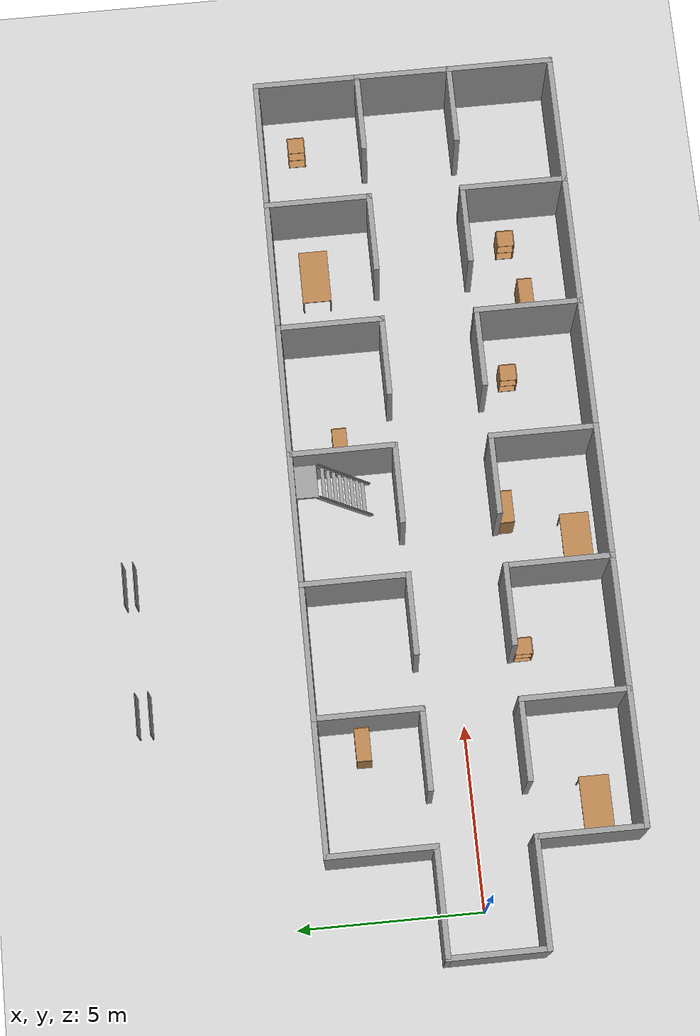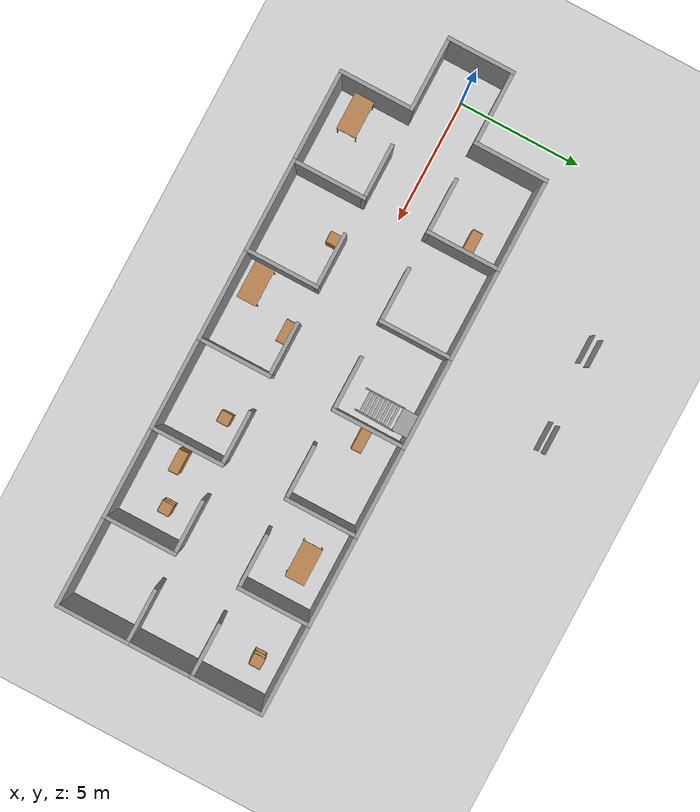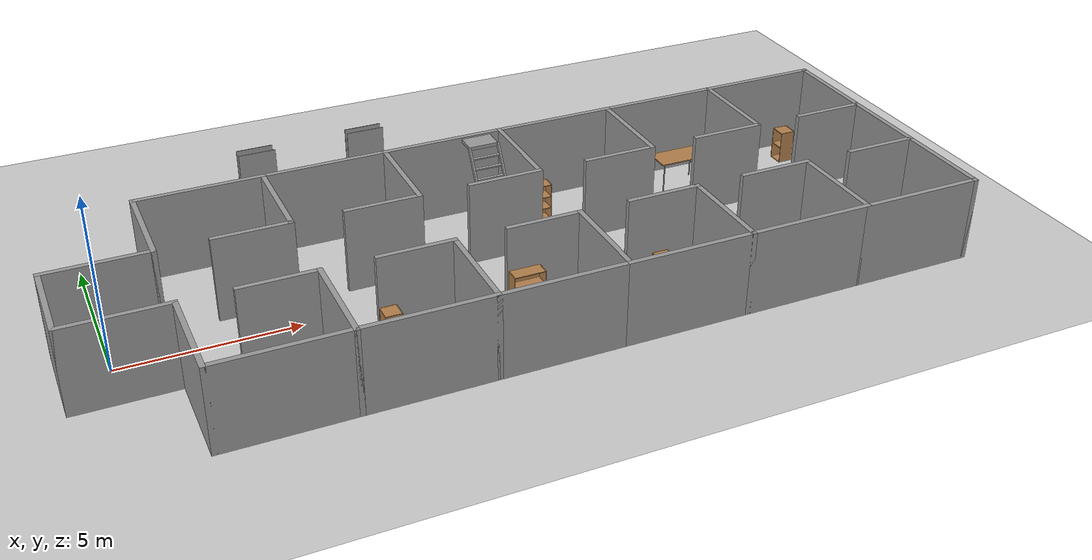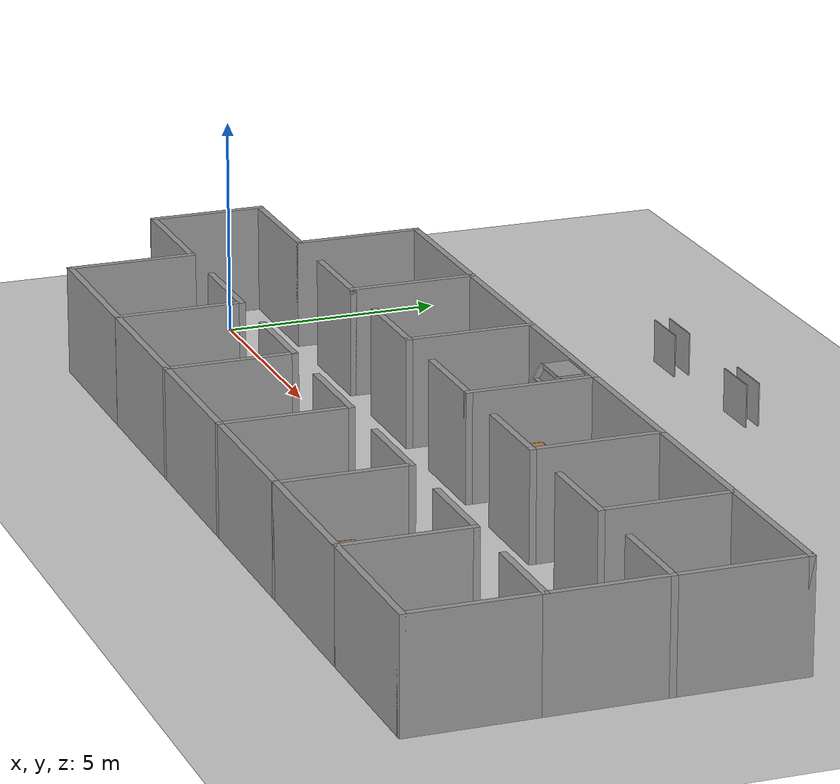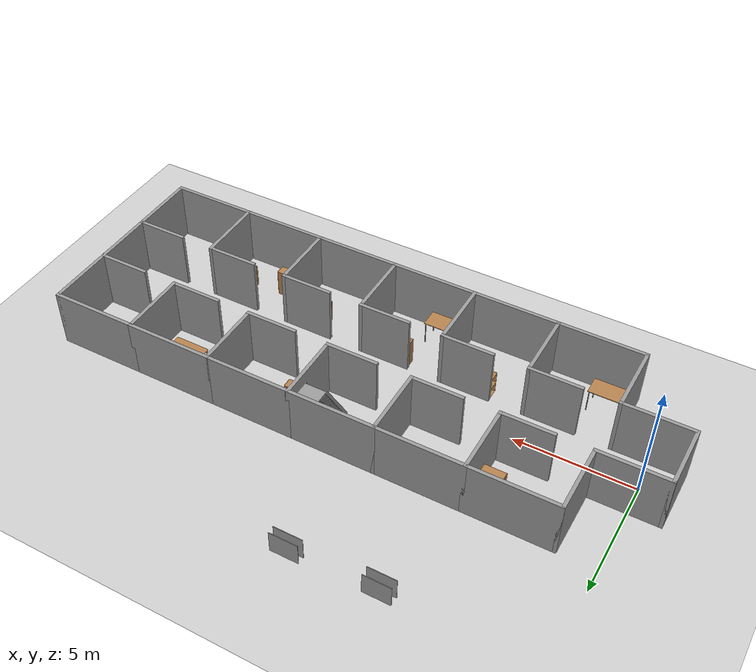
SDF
<sdf version="1.7">
 <world name="default">
  <light name="sun" type="directional">
   <pose>0 0 10 0 -0 0</pose>
   <diffuse>0.8 0.8 0.8 1</diffuse>
   <specular>0.2 0.2 0.2 1</specular>
   <attenuation>
    <range>1000</range>
    <constant>0.9</constant>
    <linear>0.01</linear>
    <quadratic>0.001</quadratic>
   </attenuation>
   <direction>-0.5 0.1 -0.9</direction>
   <spot><inner_angle>0</inner_angle><outer_angle>0</outer_angle><falloff>0</falloff></spot>
  </light>
  <model name="ground_plane">
   <static>1</static>
   <link name="link">
    <collision name="collision">
     <geometry><plane><normal>0 0 1</normal><size>100 100</size></plane></geometry>
     <surface><friction><ode><mu>100</mu><mu2>50</mu2></ode></friction></surface>
    </collision>
    <visual name="visual">
     <cast_shadows>0</cast_shadows>
     <geometry><plane><normal>0 0 1</normal><size>100 100</size></plane></geometry>
     <material>
      <script><uri>file://media/materials/scripts/gazebo.material</uri><name>Gazebo/Grey</name></script>
     </material>
    </visual>
   </link>
  </model>
  <gravity>0 0 -9.8</gravity>
  <magnetic_field>6e-06 2.3e-05 -4.2e-05</magnetic_field>
  <atmosphere type="adiabatic"/>
  <physics type="ode">
   <max_step_size>0.001</max_step_size>
   <real_time_factor>1</real_time_factor>
   <real_time_update_rate>1000</real_time_update_rate>
  </physics>
  <scene><ambient>0.4 0.4 0.4 1</ambient><background>0.7 0.7 0.7 1</background><shadows>1</shadows></scene>
  <spherical_coordinates>
   <surface_model>EARTH_WGS84</surface_model>
   <latitude_deg>0</latitude_deg>
   <longitude_deg>0</longitude_deg>
   <elevation>0</elevation>
   <heading_deg>0</heading_deg>
  </spherical_coordinates>
  <model name="indoors_hotal">
   <pose>10.9758 -0.129699 0 0 -0 0</pose>
   <link name="Wall_0">
    <collision name="Wall_0_Collision">
     <geometry><box><size>2.75 0.15 2.5</size></box></geometry>
     <pose>0 0 1.25 0 -0 0</pose>
    </collision>
    <visual name="Wall_0_Visual">
     <pose>0 0 1.25 0 -0 0</pose>
     <geometry><box><size>2.75 0.15 2.5</size></box></geometry>
     <material>
      <script><uri>file://media/materials/scripts/gazebo.material</uri><name>Gazebo/Grey</name></script>
      <ambient>1 1 1 1</ambient>
     </material>
     <meta><layer>0</layer></meta>
    </visual>
    <pose>-12.225 -0 0 0 -0 -1.5708</pose>
   </link>
   <link name="Wall_10">
    <collision name="Wall_10_Collision">
     <geometry><box><size>3 0.15 2.5</size></box></geometry>
     <pose>0 0 1.25 0 -0 0</pose>
    </collision>
    <visual name="Wall_10_Visual">
     <pose>0 0 1.25 0 -0 0</pose>
     <geometry><box><size>3 0.15 2.5</size></box></geometry>
     <material>
      <script><uri>file://media/materials/scripts/gazebo.material</uri><name>Gazebo/Grey</name></script>
      <ambient>1 1 1 1</ambient>
     </material>
     <meta><layer>0</layer></meta>
    </visual>
    <pose>-9.375 2.725 0 0 -0 1.5708</pose>
   </link>
   <link name="Wall_11">
    <collision name="Wall_11_Collision">
     <geometry><box><size>3.75 0.15 2.5</size></box></geometry>
     <pose>0 0 1.25 0 -0 0</pose>
    </collision>
    <visual name="Wall_11_Visual">
     <pose>0 0 1.25 0 -0 0</pose>
     <geometry><box><size>3.75 0.15 2.5</size></box></geometry>
     <material>
      <script><uri>file://media/materials/scripts/gazebo.material</uri><name>Gazebo/Grey</name></script>
      <ambient>1 1 1 1</ambient>
     </material>
     <meta><layer>0</layer></meta>
    </visual>
    <pose>-7.575 4.15 0 0 -0 0</pose>
   </link>
   <link name="Wall_12">
    <collision name="Wall_12_Collision">
     <geometry><box><size>3 0.15 2.5</size></box></geometry>
     <pose>0 0 1.25 0 -0 0</pose>
    </collision>
    <visual name="Wall_12_Visual">
     <pose>0 0 1.25 0 -0 0</pose>
     <geometry><box><size>3 0.15 2.5</size></box></geometry>
     <material>
      <script><uri>file://media/materials/scripts/gazebo.material</uri><name>Gazebo/Grey</name></script>
      <ambient>1 1 1 1</ambient>
     </material>
     <meta><layer>0</layer></meta>
    </visual>
    <pose>-5.775 2.725 0 0 -0 -1.5708</pose>
   </link>
   <link name="Wall_13">
    <collision name="Wall_13_Collision">
     <geometry><box><size>2.25 0.15 2.5</size></box></geometry>
     <pose>0 0 1.25 0 -0 0</pose>
    </collision>
    <visual name="Wall_13_Visual">
     <pose>0 0 1.25 0 -0 0</pose>
     <geometry><box><size>2.25 0.15 2.5</size></box></geometry>
     <material>
      <script><uri>file://media/materials/scripts/gazebo.material</uri><name>Gazebo/Grey</name></script>
      <ambient>1 1 1 1</ambient>
     </material>
     <meta><layer>0</layer></meta>
    </visual>
    <pose>-6.825 1.3 0 0 -0 3.14159</pose>
   </link>
   <link name="Wall_15">
    <collision name="Wall_15_Collision">
     <geometry><box><size>3.75 0.15 2.5</size></box></geometry>
     <pose>0 0 1.25 0 -0 0</pose>
    </collision>
    <visual name="Wall_15_Visual">
     <pose>0 0 1.25 0 -0 0</pose>
     <geometry><box><size>3.75 0.15 2.5</size></box></geometry>
     <material>
      <script><uri>file://media/materials/scripts/gazebo.material</uri><name>Gazebo/Grey</name></script>
      <ambient>1 1 1 1</ambient>
     </material>
     <meta><layer>0</layer></meta>
    </visual>
    <pose>-3.975 4.15 0 0 -0 0</pose>
   </link>
   <link name="Wall_16">
    <collision name="Wall_16_Collision">
     <geometry><box><size>3 0.15 2.5</size></box></geometry>
     <pose>0 0 1.25 0 -0 0</pose>
    </collision>
    <visual name="Wall_16_Visual">
     <pose>0 0 1.25 0 -0 0</pose>
     <geometry><box><size>3 0.15 2.5</size></box></geometry>
     <material>
      <script><uri>file://media/materials/scripts/gazebo.material</uri><name>Gazebo/Grey</name></script>
      <ambient>1 1 1 1</ambient>
     </material>
     <meta><layer>0</layer></meta>
    </visual>
    <pose>-2.175 2.725 0 0 -0 -1.5708</pose>
   </link>
   <link name="Wall_17">
    <collision name="Wall_17_Collision">
     <geometry><box><size>2.25 0.15 2.5</size></box></geometry>
     <pose>0 0 1.25 0 -0 0</pose>
    </collision>
    <visual name="Wall_17_Visual">
     <pose>0 0 1.25 0 -0 0</pose>
     <geometry><box><size>2.25 0.15 2.5</size></box></geometry>
     <material>
      <script><uri>file://media/materials/scripts/gazebo.material</uri><name>Gazebo/Grey</name></script>
      <ambient>1 1 1 1</ambient>
     </material>
     <meta><layer>0</layer></meta>
    </visual>
    <pose>-3.225 1.3 0 0 -0 3.14159</pose>
   </link>
   <link name="Wall_19">
    <collision name="Wall_19_Collision">
     <geometry><box><size>3.75 0.15 2.5</size></box></geometry>
     <pose>0 0 1.25 0 -0 0</pose>
    </collision>
    <visual name="Wall_19_Visual">
     <pose>0 0 1.25 0 -0 0</pose>
     <geometry><box><size>3.75 0.15 2.5</size></box></geometry>
     <material>
      <script><uri>file://media/materials/scripts/gazebo.material</uri><name>Gazebo/Grey</name></script>
      <ambient>1 1 1 1</ambient>
     </material>
     <meta><layer>0</layer></meta>
    </visual>
    <pose>-3.975 -4.15 0 0 -0 0</pose>
   </link>
   <link name="Wall_2">
    <collision name="Wall_2_Collision">
     <geometry><box><size>3 0.15 2.5</size></box></geometry>
     <pose>0 0 1.25 0 -0 0</pose>
    </collision>
    <visual name="Wall_2_Visual">
     <pose>0 0 1.25 0 -0 0</pose>
     <geometry><box><size>3 0.15 2.5</size></box></geometry>
     <material>
      <script><uri>file://media/materials/scripts/gazebo.material</uri><name>Gazebo/Grey</name></script>
      <ambient>1 1 1 1</ambient>
     </material>
     <meta><layer>0</layer></meta>
    </visual>
    <pose>-10.8 -1.3 0 0 -0 0</pose>
   </link>
   <link name="Wall_20">
    <collision name="Wall_20_Collision">
     <geometry><box><size>3 0.15 2.5</size></box></geometry>
     <pose>0 0 1.25 0 -0 0</pose>
    </collision>
    <visual name="Wall_20_Visual">
     <pose>0 0 1.25 0 -0 0</pose>
     <geometry><box><size>3 0.15 2.5</size></box></geometry>
     <material>
      <script><uri>file://media/materials/scripts/gazebo.material</uri><name>Gazebo/Grey</name></script>
      <ambient>1 1 1 1</ambient>
     </material>
     <meta><layer>0</layer></meta>
    </visual>
    <pose>-2.175 -2.725 0 0 -0 1.5708</pose>
   </link>
   <link name="Wall_21">
    <collision name="Wall_21_Collision">
     <geometry><box><size>2.25 0.15 2.5</size></box></geometry>
     <pose>0 0 1.25 0 -0 0</pose>
    </collision>
    <visual name="Wall_21_Visual">
     <pose>0 0 1.25 0 -0 0</pose>
     <geometry><box><size>2.25 0.15 2.5</size></box></geometry>
     <material>
      <script><uri>file://media/materials/scripts/gazebo.material</uri><name>Gazebo/Grey</name></script>
      <ambient>1 1 1 1</ambient>
     </material>
     <meta><layer>0</layer></meta>
    </visual>
    <pose>-3.225 -1.3 0 0 -0 3.14159</pose>
   </link>
   <link name="Wall_23">
    <collision name="Wall_23_Collision">
     <geometry><box><size>3.75 0.15 2.5</size></box></geometry>
     <pose>0 0 1.25 0 -0 0</pose>
    </collision>
    <visual name="Wall_23_Visual">
     <pose>0 0 1.25 0 -0 0</pose>
     <geometry><box><size>3.75 0.15 2.5</size></box></geometry>
     <material>
      <script><uri>file://media/materials/scripts/gazebo.material</uri><name>Gazebo/Grey</name></script>
      <ambient>1 1 1 1</ambient>
     </material>
     <meta><layer>0</layer></meta>
    </visual>
    <pose>-0.375 4.15 0 0 -0 0</pose>
   </link>
   <link name="Wall_24">
    <collision name="Wall_24_Collision">
     <geometry><box><size>3 0.15 2.5</size></box></geometry>
     <pose>0 0 1.25 0 -0 0</pose>
    </collision>
    <visual name="Wall_24_Visual">
     <pose>0 0 1.25 0 -0 0</pose>
     <geometry><box><size>3 0.15 2.5</size></box></geometry>
     <material>
      <script><uri>file://media/materials/scripts/gazebo.material</uri><name>Gazebo/Grey</name></script>
      <ambient>1 1 1 1</ambient>
     </material>
     <meta><layer>0</layer></meta>
    </visual>
    <pose>1.425 2.725 0 0 -0 -1.5708</pose>
   </link>
   <link name="Wall_25">
    <collision name="Wall_25_Collision">
     <geometry><box><size>2.25 0.15 2.5</size></box></geometry>
     <pose>0 0 1.25 0 -0 0</pose>
    </collision>
    <visual name="Wall_25_Visual">
     <pose>0 0 1.25 0 -0 0</pose>
     <geometry><box><size>2.25 0.15 2.5</size></box></geometry>
     <material>
      <script><uri>file://media/materials/scripts/gazebo.material</uri><name>Gazebo/Grey</name></script>
      <ambient>1 1 1 1</ambient>
     </material>
     <meta><layer>0</layer></meta>
    </visual>
    <pose>0.375 1.3 0 0 -0 3.14159</pose>
   </link>
   <link name="Wall_27">
    <collision name="Wall_27_Collision">
     <geometry><box><size>3.75 0.15 2.5</size></box></geometry>
     <pose>0 0 1.25 0 -0 0</pose>
    </collision>
    <visual name="Wall_27_Visual">
     <pose>0 0 1.25 0 -0 0</pose>
     <geometry><box><size>3.75 0.15 2.5</size></box></geometry>
     <material>
      <script><uri>file://media/materials/scripts/gazebo.material</uri><name>Gazebo/Grey</name></script>
      <ambient>1 1 1 1</ambient>
     </material>
     <meta><layer>0</layer></meta>
    </visual>
    <pose>-0.375 -4.15 0 0 -0 0</pose>
   </link>
   <link name="Wall_28">
    <collision name="Wall_28_Collision">
     <geometry><box><size>3 0.15 2.5</size></box></geometry>
     <pose>0 0 1.25 0 -0 0</pose>
    </collision>
    <visual name="Wall_28_Visual">
     <pose>0 0 1.25 0 -0 0</pose>
     <geometry><box><size>3 0.15 2.5</size></box></geometry>
     <material>
      <script><uri>file://media/materials/scripts/gazebo.material</uri><name>Gazebo/Grey</name></script>
      <ambient>1 1 1 1</ambient>
     </material>
     <meta><layer>0</layer></meta>
    </visual>
    <pose>1.425 -2.725 0 0 -0 1.5708</pose>
   </link>
   <link name="Wall_29">
    <collision name="Wall_29_Collision">
     <geometry><box><size>2.25 0.15 2.5</size></box></geometry>
     <pose>0 0 1.25 0 -0 0</pose>
    </collision>
    <visual name="Wall_29_Visual">
     <pose>0 0 1.25 0 -0 0</pose>
     <geometry><box><size>2.25 0.15 2.5</size></box></geometry>
     <material>
      <script><uri>file://media/materials/scripts/gazebo.material</uri><name>Gazebo/Grey</name></script>
      <ambient>1 1 1 1</ambient>
     </material>
     <meta><layer>0</layer></meta>
    </visual>
    <pose>0.375 -1.3 0 0 -0 3.14159</pose>
   </link>
   <link name="Wall_31">
    <collision name="Wall_31_Collision">
     <geometry><box><size>3.75 0.15 2.5</size></box></geometry>
     <pose>0 0 1.25 0 -0 0</pose>
    </collision>
    <visual name="Wall_31_Visual">
     <pose>0 0 1.25 0 -0 0</pose>
     <geometry><box><size>3.75 0.15 2.5</size></box></geometry>
     <material>
      <script><uri>file://media/materials/scripts/gazebo.material</uri><name>Gazebo/Grey</name></script>
      <ambient>1 1 1 1</ambient>
     </material>
     <meta><layer>0</layer></meta>
    </visual>
    <pose>3.225 4.15 0 0 -0 0</pose>
   </link>
   <link name="Wall_32">
    <collision name="Wall_32_Collision">
     <geometry><box><size>3 0.15 2.5</size></box></geometry>
     <pose>0 0 1.25 0 -0 0</pose>
    </collision>
    <visual name="Wall_32_Visual">
     <pose>0 0 1.25 0 -0 0</pose>
     <geometry><box><size>3 0.15 2.5</size></box></geometry>
     <material>
      <script><uri>file://media/materials/scripts/gazebo.material</uri><name>Gazebo/Grey</name></script>
      <ambient>1 1 1 1</ambient>
     </material>
     <meta><layer>0</layer></meta>
    </visual>
    <pose>5.025 2.725 0 0 -0 -1.5708</pose>
   </link>
   <link name="Wall_33">
    <collision name="Wall_33_Collision">
     <geometry><box><size>2.25 0.15 2.5</size></box></geometry>
     <pose>0 0 1.25 0 -0 0</pose>
    </collision>
    <visual name="Wall_33_Visual">
     <pose>0 0 1.25 0 -0 0</pose>
     <geometry><box><size>2.25 0.15 2.5</size></box></geometry>
     <material>
      <script><uri>file://media/materials/scripts/gazebo.material</uri><name>Gazebo/Grey</name></script>
      <ambient>1 1 1 1</ambient>
     </material>
     <meta><layer>0</layer></meta>
    </visual>
    <pose>3.975 1.3 0 0 -0 3.14159</pose>
   </link>
   <link name="Wall_35">
    <collision name="Wall_35_Collision">
     <geometry><box><size>3.75 0.15 2.5</size></box></geometry>
     <pose>0 0 1.25 0 -0 0</pose>
    </collision>
    <visual name="Wall_35_Visual">
     <pose>0 0 1.25 0 -0 0</pose>
     <geometry><box><size>3.75 0.15 2.5</size></box></geometry>
     <material>
      <script><uri>file://media/materials/scripts/gazebo.material</uri><name>Gazebo/Grey</name></script>
      <ambient>1 1 1 1</ambient>
     </material>
     <meta><layer>0</layer></meta>
    </visual>
    <pose>6.825 4.15 0 0 -0 0</pose>
   </link>
   <link name="Wall_36">
    <collision name="Wall_36_Collision">
     <geometry><box><size>3 0.15 2.5</size></box></geometry>
     <pose>0 0 1.25 0 -0 0</pose>
    </collision>
    <visual name="Wall_36_Visual">
     <pose>0 0 1.25 0 -0 0</pose>
     <geometry><box><size>3 0.15 2.5</size></box></geometry>
     <material>
      <script><uri>file://media/materials/scripts/gazebo.material</uri><name>Gazebo/Grey</name></script>
      <ambient>1 1 1 1</ambient>
     </material>
     <meta><layer>0</layer></meta>
    </visual>
    <pose>8.625 2.725 0 0 -0 -1.5708</pose>
   </link>
   <link name="Wall_37">
    <collision name="Wall_37_Collision">
     <geometry><box><size>2.25 0.15 2.5</size></box></geometry>
     <pose>0 0 1.25 0 -0 0</pose>
    </collision>
    <visual name="Wall_37_Visual">
     <pose>0 0 1.25 0 -0 0</pose>
     <geometry><box><size>2.25 0.15 2.5</size></box></geometry>
     <material>
      <script><uri>file://media/materials/scripts/gazebo.material</uri><name>Gazebo/Grey</name></script>
      <ambient>1 1 1 1</ambient>
     </material>
     <meta><layer>0</layer></meta>
    </visual>
    <pose>7.575 1.3 0 0 -0 3.14159</pose>
   </link>
   <link name="Wall_39">
    <collision name="Wall_39_Collision">
     <geometry><box><size>3.75 0.15 2.5</size></box></geometry>
     <pose>0 0 1.25 0 -0 0</pose>
    </collision>
    <visual name="Wall_39_Visual">
     <pose>0 0 1.25 0 -0 0</pose>
     <geometry><box><size>3.75 0.15 2.5</size></box></geometry>
     <material>
      <script><uri>file://media/materials/scripts/gazebo.material</uri><name>Gazebo/Grey</name></script>
      <ambient>1 1 1 1</ambient>
     </material>
     <meta><layer>0</layer></meta>
    </visual>
    <pose>10.425 4.15 0 0 -0 0</pose>
   </link>
   <link name="Wall_4">
    <collision name="Wall_4_Collision">
     <geometry><box><size>3 0.15 2.5</size></box></geometry>
     <pose>0 0 1.25 0 -0 0</pose>
    </collision>
    <visual name="Wall_4_Visual">
     <pose>0 0 1.25 0 -0 0</pose>
     <geometry><box><size>3 0.15 2.5</size></box></geometry>
     <material>
      <script><uri>file://media/materials/scripts/gazebo.material</uri><name>Gazebo/Grey</name></script>
      <ambient>1 1 1 1</ambient>
     </material>
     <meta><layer>0</layer></meta>
    </visual>
    <pose>-9.375 -2.725 0 0 -0 -1.5708</pose>
   </link>
   <link name="Wall_40">
    <collision name="Wall_40_Collision">
     <geometry><box><size>3 0.15 2.5</size></box></geometry>
     <pose>0 0 1.25 0 -0 0</pose>
    </collision>
    <visual name="Wall_40_Visual">
     <pose>0 0 1.25 0 -0 0</pose>
     <geometry><box><size>3 0.15 2.5</size></box></geometry>
     <material>
      <script><uri>file://media/materials/scripts/gazebo.material</uri><name>Gazebo/Grey</name></script>
      <ambient>1 1 1 1</ambient>
     </material>
     <meta><layer>0</layer></meta>
    </visual>
    <pose>12.225 2.725 0 0 -0 -1.5708</pose>
   </link>
   <link name="Wall_41">
    <collision name="Wall_41_Collision">
     <geometry><box><size>2.25 0.15 2.5</size></box></geometry>
     <pose>0 0 1.25 0 -0 0</pose>
    </collision>
    <visual name="Wall_41_Visual">
     <pose>0 0 1.25 0 -0 0</pose>
     <geometry><box><size>2.25 0.15 2.5</size></box></geometry>
     <material>
      <script><uri>file://media/materials/scripts/gazebo.material</uri><name>Gazebo/Grey</name></script>
      <ambient>1 1 1 1</ambient>
     </material>
     <meta><layer>0</layer></meta>
    </visual>
    <pose>11.175 1.3 0 0 -0 3.14159</pose>
   </link>
   <link name="Wall_43">
    <collision name="Wall_43_Collision">
     <geometry><box><size>3.75 0.15 2.5</size></box></geometry>
     <pose>0 0 1.25 0 -0 0</pose>
    </collision>
    <visual name="Wall_43_Visual">
     <pose>0 0 1.25 0 -0 0</pose>
     <geometry><box><size>3.75 0.15 2.5</size></box></geometry>
     <material>
      <script><uri>file://media/materials/scripts/gazebo.material</uri><name>Gazebo/Grey</name></script>
      <ambient>1 1 1 1</ambient>
     </material>
     <meta><layer>0</layer></meta>
    </visual>
    <pose>3.225 -4.15 0 0 -0 0</pose>
   </link>
   <link name="Wall_44">
    <collision name="Wall_44_Collision">
     <geometry><box><size>3 0.15 2.5</size></box></geometry>
     <pose>0 0 1.25 0 -0 0</pose>
    </collision>
    <visual name="Wall_44_Visual">
     <pose>0 0 1.25 0 -0 0</pose>
     <geometry><box><size>3 0.15 2.5</size></box></geometry>
     <material>
      <script><uri>file://media/materials/scripts/gazebo.material</uri><name>Gazebo/Grey</name></script>
      <ambient>1 1 1 1</ambient>
     </material>
     <meta><layer>0</layer></meta>
    </visual>
    <pose>5.025 -2.725 0 0 -0 1.5708</pose>
   </link>
   <link name="Wall_45">
    <collision name="Wall_45_Collision">
     <geometry><box><size>2.25 0.15 2.5</size></box></geometry>
     <pose>0 0 1.25 0 -0 0</pose>
    </collision>
    <visual name="Wall_45_Visual">
     <pose>0 0 1.25 0 -0 0</pose>
     <geometry><box><size>2.25 0.15 2.5</size></box></geometry>
     <material>
      <script><uri>file://media/materials/scripts/gazebo.material</uri><name>Gazebo/Grey</name></script>
      <ambient>1 1 1 1</ambient>
     </material>
     <meta><layer>0</layer></meta>
    </visual>
    <pose>3.975 -1.3 0 0 -0 3.14159</pose>
   </link>
   <link name="Wall_47">
    <collision name="Wall_47_Collision">
     <geometry><box><size>3.75 0.15 2.5</size></box></geometry>
     <pose>0 0 1.25 0 -0 0</pose>
    </collision>
    <visual name="Wall_47_Visual">
     <pose>0 0 1.25 0 -0 0</pose>
     <geometry><box><size>3.75 0.15 2.5</size></box></geometry>
     <material>
      <script><uri>file://media/materials/scripts/gazebo.material</uri><name>Gazebo/Grey</name></script>
      <ambient>1 1 1 1</ambient>
     </material>
     <meta><layer>0</layer></meta>
    </visual>
    <pose>6.825 -4.15 0 0 -0 0</pose>
   </link>
   <link name="Wall_48">
    <collision name="Wall_48_Collision">
     <geometry><box><size>3 0.15 2.5</size></box></geometry>
     <pose>0 0 1.25 0 -0 0</pose>
    </collision>
    <visual name="Wall_48_Visual">
     <pose>0 0 1.25 0 -0 0</pose>
     <geometry><box><size>3 0.15 2.5</size></box></geometry>
     <material>
      <script><uri>file://media/materials/scripts/gazebo.material</uri><name>Gazebo/Grey</name></script>
      <ambient>1 1 1 1</ambient>
     </material>
     <meta><layer>0</layer></meta>
    </visual>
    <pose>8.625 -2.725 0 0 -0 1.5708</pose>
   </link>
   <link name="Wall_49">
    <collision name="Wall_49_Collision">
     <geometry><box><size>2.25 0.15 2.5</size></box></geometry>
     <pose>0 0 1.25 0 -0 0</pose>
    </collision>
    <visual name="Wall_49_Visual">
     <pose>0 0 1.25 0 -0 0</pose>
     <geometry><box><size>2.25 0.15 2.5</size></box></geometry>
     <material>
      <script><uri>file://media/materials/scripts/gazebo.material</uri><name>Gazebo/Grey</name></script>
      <ambient>1 1 1 1</ambient>
     </material>
     <meta><layer>0</layer></meta>
    </visual>
    <pose>7.575 -1.3 0 0 -0 3.14159</pose>
   </link>
   <link name="Wall_5">
    <collision name="Wall_5_Collision">
     <geometry><box><size>3.75 0.15 2.5</size></box></geometry>
     <pose>0 0 1.25 0 -0 0</pose>
    </collision>
    <visual name="Wall_5_Visual">
     <pose>0 0 1.25 0 -0 0</pose>
     <geometry><box><size>3.75 0.15 2.5</size></box></geometry>
     <material>
      <script><uri>file://media/materials/scripts/gazebo.material</uri><name>Gazebo/Grey</name></script>
      <ambient>1 1 1 1</ambient>
     </material>
     <meta><layer>0</layer></meta>
    </visual>
    <pose>-7.575 -4.15 0 0 -0 0</pose>
   </link>
   <link name="Wall_51">
    <collision name="Wall_51_Collision">
     <geometry><box><size>3.75 0.15 2.5</size></box></geometry>
     <pose>0 0 1.25 0 -0 0</pose>
    </collision>
    <visual name="Wall_51_Visual">
     <pose>0 0 1.25 0 -0 0</pose>
     <geometry><box><size>3.75 0.15 2.5</size></box></geometry>
     <material>
      <script><uri>file://media/materials/scripts/gazebo.material</uri><name>Gazebo/Grey</name></script>
      <ambient>1 1 1 1</ambient>
     </material>
     <meta><layer>0</layer></meta>
    </visual>
    <pose>10.425 -4.15 0 0 -0 0</pose>
   </link>
   <link name="Wall_52">
    <collision name="Wall_52_Collision">
     <geometry><box><size>3 0.15 2.5</size></box></geometry>
     <pose>0 0 1.25 0 -0 0</pose>
    </collision>
    <visual name="Wall_52_Visual">
     <pose>0 0 1.25 0 -0 0</pose>
     <geometry><box><size>3 0.15 2.5</size></box></geometry>
     <material>
      <script><uri>file://media/materials/scripts/gazebo.material</uri><name>Gazebo/Grey</name></script>
      <ambient>1 1 1 1</ambient>
     </material>
     <meta><layer>0</layer></meta>
    </visual>
    <pose>12.225 -2.725 0 0 -0 1.5708</pose>
   </link>
   <link name="Wall_53">
    <collision name="Wall_53_Collision">
     <geometry><box><size>2.25 0.15 2.5</size></box></geometry>
     <pose>0 0 1.25 0 -0 0</pose>
    </collision>
    <visual name="Wall_53_Visual">
     <pose>0 0 1.25 0 -0 0</pose>
     <geometry><box><size>2.25 0.15 2.5</size></box></geometry>
     <material>
      <script><uri>file://media/materials/scripts/gazebo.material</uri><name>Gazebo/Grey</name></script>
      <ambient>1 1 1 1</ambient>
     </material>
     <meta><layer>0</layer></meta>
    </visual>
    <pose>11.175 -1.3 0 0 -0 3.14159</pose>
   </link>
   <link name="Wall_55">
    <collision name="Wall_55_Collision">
     <geometry><box><size>2.75 0.15 2.5</size></box></geometry>
     <pose>0 0 1.25 0 -0 0</pose>
    </collision>
    <visual name="Wall_55_Visual">
     <pose>0 0 1.25 0 -0 0</pose>
     <geometry><box><size>2.75 0.15 2.5</size></box></geometry>
     <material>
      <script><uri>file://media/materials/scripts/gazebo.material</uri><name>Gazebo/Grey</name></script>
      <ambient>1 1 1 1</ambient>
     </material>
     <meta><layer>0</layer></meta>
    </visual>
    <pose>12.225 -0 0 0 -0 1.5708</pose>
   </link>
   <link name="Wall_6">
    <collision name="Wall_6_Collision">
     <geometry><box><size>3 0.15 2.5</size></box></geometry>
     <pose>0 0 1.25 0 -0 0</pose>
    </collision>
    <visual name="Wall_6_Visual">
     <pose>0 0 1.25 0 -0 0</pose>
     <geometry><box><size>3 0.15 2.5</size></box></geometry>
     <material>
      <script><uri>file://media/materials/scripts/gazebo.material</uri><name>Gazebo/Grey</name></script>
      <ambient>1 1 1 1</ambient>
     </material>
     <meta><layer>0</layer></meta>
    </visual>
    <pose>-5.775 -2.725 0 0 -0 1.5708</pose>
   </link>
   <link name="Wall_7">
    <collision name="Wall_7_Collision">
     <geometry><box><size>2.25 0.15 2.5</size></box></geometry>
     <pose>0 0 1.25 0 -0 0</pose>
    </collision>
    <visual name="Wall_7_Visual">
     <pose>0 0 1.25 0 -0 0</pose>
     <geometry><box><size>2.25 0.15 2.5</size></box></geometry>
     <material>
      <script><uri>file://media/materials/scripts/gazebo.material</uri><name>Gazebo/Grey</name></script>
      <ambient>1 1 1 1</ambient>
     </material>
     <meta><layer>0</layer></meta>
    </visual>
    <pose>-6.825 -1.3 0 0 -0 3.14159</pose>
   </link>
   <link name="Wall_9">
    <collision name="Wall_9_Collision">
     <geometry><box><size>3 0.15 2.5</size></box></geometry>
     <pose>0 0 1.25 0 -0 0</pose>
    </collision>
    <visual name="Wall_9_Visual">
     <pose>0 0 1.25 0 -0 0</pose>
     <geometry><box><size>3 0.15 2.5</size></box></geometry>
     <material>
      <script><uri>file://media/materials/scripts/gazebo.material</uri><name>Gazebo/Grey</name></script>
      <ambient>1 1 1 1</ambient>
     </material>
     <meta><layer>0</layer></meta>
    </visual>
    <pose>-10.8 1.3 0 0 -0 0</pose>
   </link>
   <static>1</static>
  </model>
  <model name="bookshelf">
   <static>1</static>
   <link name="link">
    <inertial><mass>1</mass></inertial>
    <collision name="back">
     <pose>0 0.005 0.6 0 -0 0</pose>
     <geometry><box><size>0.9 0.01 1.2</size></box></geometry>
    </collision>
    <visual name="visual1">
     <pose>0 0.005 0.6 0 -0 0</pose>
     <geometry><box><size>0.9 0.01 1.2</size></box></geometry>
     <material>
      <script><uri>file://media/materials/scripts/gazebo.material</uri><name>Gazebo/Wood</name></script>
     </material>
    </visual>
    <collision name="left_side">
     <pose>0.45 -0.195 0.6 0 -0 0</pose>
     <geometry><box><size>0.02 0.4 1.2</size></box></geometry>
    </collision>
    <visual name="visual2">
     <pose>0.45 -0.195 0.6 0 -0 0</pose>
     <geometry><box><size>0.02 0.4 1.2</size></box></geometry>
     <material>
      <script><uri>file://media/materials/scripts/gazebo.material</uri><name>Gazebo/Wood</name></script>
     </material>
    </visual>
    <collision name="right_side">
     <pose>-0.45 -0.195 0.6 0 -0 0</pose>
     <geometry><box><size>0.02 0.4 1.2</size></box></geometry>
    </collision>
    <visual name="visual3">
     <pose>-0.45 -0.195 0.6 0 -0 0</pose>
     <geometry><box><size>0.02 0.4 1.2</size></box></geometry>
     <material>
      <script><uri>file://media/materials/scripts/gazebo.material</uri><name>Gazebo/Wood</name></script>
     </material>
    </visual>
    <collision name="bottom">
     <pose>0 -0.195 0.03 0 -0 0</pose>
     <geometry><box><size>0.88 0.4 0.06</size></box></geometry>
    </collision>
    <visual name="visual4">
     <pose>0 -0.195 0.03 0 -0 0</pose>
     <geometry><box><size>0.88 0.4 0.06</size></box></geometry>
     <material>
      <script><uri>file://media/materials/scripts/gazebo.material</uri><name>Gazebo/Wood</name></script>
     </material>
    </visual>
    <collision name="top">
     <pose>0 -0.195 1.19 0 -0 0</pose>
     <geometry><box><size>0.88 0.4 0.02</size></box></geometry>
    </collision>
    <visual name="visual5">
     <pose>0 -0.195 1.19 0 -0 0</pose>
     <geometry><box><size>0.88 0.4 0.02</size></box></geometry>
     <material>
      <script><uri>file://media/materials/scripts/gazebo.material</uri><name>Gazebo/Wood</name></script>
     </material>
    </visual>
    <collision name="low_shelf">
     <pose>0 -0.195 0.43 0 -0 0</pose>
     <geometry><box><size>0.88 0.4 0.02</size></box></geometry>
    </collision>
    <visual name="visual6">
     <pose>0 -0.195 0.43 0 -0 0</pose>
     <geometry><box><size>0.88 0.4 0.02</size></box></geometry>
     <material>
      <script><uri>file://media/materials/scripts/gazebo.material</uri><name>Gazebo/Wood</name></script>
     </material>
    </visual>
    <collision name="high_shelf">
     <pose>0 -0.195 0.8 0 -0 0</pose>
     <geometry><box><size>0.88 0.4 0.02</size></box></geometry>
    </collision>
    <visual name="visual7">
     <pose>0 -0.195 0.8 0 -0 0</pose>
     <geometry><box><size>0.88 0.4 0.02</size></box></geometry>
     <material>
      <script><uri>file://media/materials/scripts/gazebo.material</uri><name>Gazebo/Wood</name></script>
     </material>
    </visual>
   </link>
   <pose>12.9298 2.8146 0 0 -0 0</pose>
  </model>
  <model name="cabinet">
   <static>1</static>
   <link name="cabinet_bottom_plate">
    <inertial>
     <pose>0 0 -1 0 -0 0</pose>
     <inertia><ixx>2.05</ixx><ixy>0</ixy><ixz>0</ixz><iyy>2.05</iyy><iyz>0</iyz><izz>2.05</izz></inertia>
     <mass>25</mass>
    </inertial>
    <collision name="cabinet_bottom_plate_geom">
     <pose>0 0 0.01 0 -0 0</pose>
     <geometry><box><size>0.45 0.45 0.02</size></box></geometry>
    </collision>
    <visual name="cabinet_bottom_plate_geom_visual">
     <pose>0 0 0.01 0 -0 0</pose>
     <geometry><box><size>0.45 0.45 0.02</size></box></geometry>
     <material>
      <script><uri>file://media/materials/scripts/gazebo.material</uri><name>Gazebo/Wood</name></script>
     </material>
    </visual>
    <collision name="cabinet_bottom_plate_geom_cabinet_back_plate">
     <pose>0.235 0 0.51 0 -0 0</pose>
     <geometry><box><size>0.02 0.45 1.02</size></box></geometry>
    </collision>
    <visual name="cabinet_bottom_plate_geom_cabinet_back_plate_visual">
     <pose>0.235 0 0.51 0 -0 0</pose>
     <geometry><box><size>0.02 0.45 1.02</size></box></geometry>
     <material>
      <script><uri>file://media/materials/scripts/gazebo.material</uri><name>Gazebo/Wood</name></script>
     </material>
    </visual>
    <collision name="cabinet_bottom_plate_geom_cabinet_left_plate">
     <pose>0 0.235 0.51 0 -0 0</pose>
     <geometry><box><size>0.45 0.02 1.02</size></box></geometry>
    </collision>
    <visual name="cabinet_bottom_plate_geom_cabinet_left_plate_visual">
     <pose>0 0.235 0.51 0 -0 0</pose>
     <geometry><box><size>0.45 0.02 1.02</size></box></geometry>
     <material>
      <script><uri>file://media/materials/scripts/gazebo.material</uri><name>Gazebo/Wood</name></script>
     </material>
    </visual>
    <collision name="cabinet_bottom_plate_geom_cabinet_middle_plate">
     <pose>0 0 0.51 0 -0 0</pose>
     <geometry><box><size>0.45 0.45 0.02</size></box></geometry>
    </collision>
    <visual name="cabinet_bottom_plate_geom_cabinet_middle_plate_visual">
     <pose>0 0 0.51 0 -0 0</pose>
     <geometry><box><size>0.45 0.45 0.02</size></box></geometry>
     <material>
      <script><uri>file://media/materials/scripts/gazebo.material</uri><name>Gazebo/Wood</name></script>
     </material>
    </visual>
    <collision name="cabinet_bottom_plate_geom_cabinet_right_plate">
     <pose>0 -0.235 0.51 0 -0 0</pose>
     <geometry><box><size>0.45 0.02 1.02</size></box></geometry>
    </collision>
    <visual name="cabinet_bottom_plate_geom_cabinet_right_plate_visual">
     <pose>0 -0.235 0.51 0 -0 0</pose>
     <geometry><box><size>0.45 0.02 1.02</size></box></geometry>
     <material>
      <script><uri>file://media/materials/scripts/gazebo.material</uri><name>Gazebo/Wood</name></script>
     </material>
    </visual>
    <collision name="cabinet_bottom_plate_geom_cabinet_top_plate">
     <pose>0 0 1.01 0 -0 0</pose>
     <geometry><box><size>0.45 0.45 0.02</size></box></geometry>
    </collision>
    <visual name="cabinet_bottom_plate_geom_cabinet_top_plate_visual">
     <pose>0 0 1.01 0 -0 0</pose>
     <geometry><box><size>0.45 0.45 0.02</size></box></geometry>
     <material>
      <script><uri>file://media/materials/scripts/gazebo.material</uri><name>Gazebo/Wood</name></script>
     </material>
    </visual>
   </link>
   <pose>14.591 -2.21285 0 0 -0 0</pose>
  </model>
  <model name="cabinet_0">
   <static>1</static>
   <link name="cabinet_bottom_plate">
    <inertial>
     <pose>0 0 -1 0 -0 0</pose>
     <inertia><ixx>2.05</ixx><ixy>0</ixy><ixz>0</ixz><iyy>2.05</iyy><iyz>0</iyz><izz>2.05</izz></inertia>
     <mass>25</mass>
    </inertial>
    <collision name="cabinet_bottom_plate_geom">
     <pose>0 0 0.01 0 -0 0</pose>
     <geometry><box><size>0.45 0.45 0.02</size></box></geometry>
    </collision>
    <visual name="cabinet_bottom_plate_geom_visual">
     <pose>0 0 0.01 0 -0 0</pose>
     <geometry><box><size>0.45 0.45 0.02</size></box></geometry>
     <material>
      <script><uri>file://media/materials/scripts/gazebo.material</uri><name>Gazebo/Wood</name></script>
     </material>
    </visual>
    <collision name="cabinet_bottom_plate_geom_cabinet_back_plate">
     <pose>0.235 0 0.51 0 -0 0</pose>
     <geometry><box><size>0.02 0.45 1.02</size></box></geometry>
    </collision>
    <visual name="cabinet_bottom_plate_geom_cabinet_back_plate_visual">
     <pose>0.235 0 0.51 0 -0 0</pose>
     <geometry><box><size>0.02 0.45 1.02</size></box></geometry>
     <material>
      <script><uri>file://media/materials/scripts/gazebo.material</uri><name>Gazebo/Wood</name></script>
     </material>
    </visual>
    <collision name="cabinet_bottom_plate_geom_cabinet_left_plate">
     <pose>0 0.235 0.51 0 -0 0</pose>
     <geometry><box><size>0.45 0.02 1.02</size></box></geometry>
    </collision>
    <visual name="cabinet_bottom_plate_geom_cabinet_left_plate_visual">
     <pose>0 0.235 0.51 0 -0 0</pose>
     <geometry><box><size>0.45 0.02 1.02</size></box></geometry>
     <material>
      <script><uri>file://media/materials/scripts/gazebo.material</uri><name>Gazebo/Wood</name></script>
     </material>
    </visual>
    <collision name="cabinet_bottom_plate_geom_cabinet_middle_plate">
     <pose>0 0 0.51 0 -0 0</pose>
     <geometry><box><size>0.45 0.45 0.02</size></box></geometry>
    </collision>
    <visual name="cabinet_bottom_plate_geom_cabinet_middle_plate_visual">
     <pose>0 0 0.51 0 -0 0</pose>
     <geometry><box><size>0.45 0.45 0.02</size></box></geometry>
     <material>
      <script><uri>file://media/materials/scripts/gazebo.material</uri><name>Gazebo/Wood</name></script>
     </material>
    </visual>
    <collision name="cabinet_bottom_plate_geom_cabinet_right_plate">
     <pose>0 -0.235 0.51 0 -0 0</pose>
     <geometry><box><size>0.45 0.02 1.02</size></box></geometry>
    </collision>
    <visual name="cabinet_bottom_plate_geom_cabinet_right_plate_visual">
     <pose>0 -0.235 0.51 0 -0 0</pose>
     <geometry><box><size>0.45 0.02 1.02</size></box></geometry>
     <material>
      <script><uri>file://media/materials/scripts/gazebo.material</uri><name>Gazebo/Wood</name></script>
     </material>
    </visual>
    <collision name="cabinet_bottom_plate_geom_cabinet_top_plate">
     <pose>0 0 1.01 0 -0 0</pose>
     <geometry><box><size>0.45 0.45 0.02</size></box></geometry>
    </collision>
    <visual name="cabinet_bottom_plate_geom_cabinet_top_plate_visual">
     <pose>0 0 1.01 0 -0 0</pose>
     <geometry><box><size>0.45 0.45 0.02</size></box></geometry>
     <material>
      <script><uri>file://media/materials/scripts/gazebo.material</uri><name>Gazebo/Wood</name></script>
     </material>
    </visual>
   </link>
   <pose>21.9346 3.05384 0 0 -0 0</pose>
  </model>
  <model name="table">
   <static>1</static>
   <link name="link">
    <collision name="surface">
     <pose>0 0 1 0 -0 0</pose>
     <geometry><box><size>1.5 0.8 0.03</size></box></geometry>
     <surface><friction><ode><mu>0.6</mu><mu2>0.6</mu2></ode></friction></surface>
    </collision>
    <visual name="visual1">
     <pose>0 0 1 0 -0 0</pose>
     <geometry><box><size>1.5 0.8 0.03</size></box></geometry>
     <material>
      <script><uri>file://media/materials/scripts/gazebo.material</uri><name>Gazebo/Wood</name></script>
     </material>
    </visual>
    <collision name="front_left_leg">
     <pose>0.68 0.38 0.5 0 -0 0</pose>
     <geometry><cylinder><radius>0.02</radius><length>1</length></cylinder></geometry>
    </collision>
    <visual name="front_left_leg">
     <pose>0.68 0.38 0.5 0 -0 0</pose>
     <geometry><cylinder><radius>0.02</radius><length>1</length></cylinder></geometry>
     <material>
      <script><uri>file://media/materials/scripts/gazebo.material</uri><name>Gazebo/Grey</name></script>
     </material>
    </visual>
    <collision name="front_right_leg">
     <pose>0.68 -0.38 0.5 0 -0 0</pose>
     <geometry><cylinder><radius>0.02</radius><length>1</length></cylinder></geometry>
    </collision>
    <visual name="front_right_leg">
     <pose>0.68 -0.38 0.5 0 -0 0</pose>
     <geometry><cylinder><radius>0.02</radius><length>1</length></cylinder></geometry>
     <material>
      <script><uri>file://media/materials/scripts/gazebo.material</uri><name>Gazebo/Grey</name></script>
     </material>
    </visual>
    <collision name="back_right_leg">
     <pose>-0.68 -0.38 0.5 0 -0 0</pose>
     <geometry><cylinder><radius>0.02</radius><length>1</length></cylinder></geometry>
    </collision>
    <visual name="back_right_leg">
     <pose>-0.68 -0.38 0.5 0 -0 0</pose>
     <geometry><cylinder><radius>0.02</radius><length>1</length></cylinder></geometry>
     <material>
      <script><uri>file://media/materials/scripts/gazebo.material</uri><name>Gazebo/Grey</name></script>
     </material>
    </visual>
    <collision name="back_left_leg">
     <pose>-0.68 0.38 0.5 0 -0 0</pose>
     <geometry><cylinder><radius>0.02</radius><length>1</length></cylinder></geometry>
    </collision>
    <visual name="back_left_leg">
     <pose>-0.68 0.38 0.5 0 -0 0</pose>
     <geometry><cylinder><radius>0.02</radius><length>1</length></cylinder></geometry>
     <material>
      <script><uri>file://media/materials/scripts/gazebo.material</uri><name>Gazebo/Grey</name></script>
     </material>
    </visual>
   </link>
   <pose>17.9308 2.86983 0 0 -0 0</pose>
  </model>
  <model name="cabinet_1">
   <static>1</static>
   <link name="cabinet_bottom_plate">
    <inertial>
     <pose>0 0 -1 0 -0 0</pose>
     <inertia><ixx>2.05</ixx><ixy>0</ixy><ixz>0</ixz><iyy>2.05</iyy><iyz>0</iyz><izz>2.05</izz></inertia>
     <mass>25</mass>
    </inertial>
    <collision name="cabinet_bottom_plate_geom">
     <pose>0 0 0.01 0 -0 0</pose>
     <geometry><box><size>0.45 0.45 0.02</size></box></geometry>
    </collision>
    <visual name="cabinet_bottom_plate_geom_visual">
     <pose>0 0 0.01 0 -0 0</pose>
     <geometry><box><size>0.45 0.45 0.02</size></box></geometry>
     <material>
      <script><uri>file://media/materials/scripts/gazebo.material</uri><name>Gazebo/Wood</name></script>
     </material>
    </visual>
    <collision name="cabinet_bottom_plate_geom_cabinet_back_plate">
     <pose>0.235 0 0.51 0 -0 0</pose>
     <geometry><box><size>0.02 0.45 1.02</size></box></geometry>
    </collision>
    <visual name="cabinet_bottom_plate_geom_cabinet_back_plate_visual">
     <pose>0.235 0 0.51 0 -0 0</pose>
     <geometry><box><size>0.02 0.45 1.02</size></box></geometry>
     <material>
      <script><uri>file://media/materials/scripts/gazebo.material</uri><name>Gazebo/Wood</name></script>
     </material>
    </visual>
    <collision name="cabinet_bottom_plate_geom_cabinet_left_plate">
     <pose>0 0.235 0.51 0 -0 0</pose>
     <geometry><box><size>0.45 0.02 1.02</size></box></geometry>
    </collision>
    <visual name="cabinet_bottom_plate_geom_cabinet_left_plate_visual">
     <pose>0 0.235 0.51 0 -0 0</pose>
     <geometry><box><size>0.45 0.02 1.02</size></box></geometry>
     <material>
      <script><uri>file://media/materials/scripts/gazebo.material</uri><name>Gazebo/Wood</name></script>
     </material>
    </visual>
    <collision name="cabinet_bottom_plate_geom_cabinet_middle_plate">
     <pose>0 0 0.51 0 -0 0</pose>
     <geometry><box><size>0.45 0.45 0.02</size></box></geometry>
    </collision>
    <visual name="cabinet_bottom_plate_geom_cabinet_middle_plate_visual">
     <pose>0 0 0.51 0 -0 0</pose>
     <geometry><box><size>0.45 0.45 0.02</size></box></geometry>
     <material>
      <script><uri>file://media/materials/scripts/gazebo.material</uri><name>Gazebo/Wood</name></script>
     </material>
    </visual>
    <collision name="cabinet_bottom_plate_geom_cabinet_right_plate">
     <pose>0 -0.235 0.51 0 -0 0</pose>
     <geometry><box><size>0.45 0.02 1.02</size></box></geometry>
    </collision>
    <visual name="cabinet_bottom_plate_geom_cabinet_right_plate_visual">
     <pose>0 -0.235 0.51 0 -0 0</pose>
     <geometry><box><size>0.45 0.02 1.02</size></box></geometry>
     <material>
      <script><uri>file://media/materials/scripts/gazebo.material</uri><name>Gazebo/Wood</name></script>
     </material>
    </visual>
    <collision name="cabinet_bottom_plate_geom_cabinet_top_plate">
     <pose>0 0 1.01 0 -0 0</pose>
     <geometry><box><size>0.45 0.45 0.02</size></box></geometry>
    </collision>
    <visual name="cabinet_bottom_plate_geom_cabinet_top_plate_visual">
     <pose>0 0 1.01 0 -0 0</pose>
     <geometry><box><size>0.45 0.45 0.02</size></box></geometry>
     <material>
      <script><uri>file://media/materials/scripts/gazebo.material</uri><name>Gazebo/Wood</name></script>
     </material>
    </visual>
   </link>
   <pose>18.5452 -2.57788 0 0 -0 0</pose>
  </model>
  <model name="bookshelf_0">
   <static>1</static>
   <link name="link">
    <inertial><mass>1</mass></inertial>
    <collision name="back">
     <pose>0 0.005 0.6 0 -0 0</pose>
     <geometry><box><size>0.9 0.01 1.2</size></box></geometry>
    </collision>
    <visual name="visual1">
     <pose>0 0.005 0.6 0 -0 0</pose>
     <geometry><box><size>0.9 0.01 1.2</size></box></geometry>
     <material>
      <script><uri>file://media/materials/scripts/gazebo.material</uri><name>Gazebo/Wood</name></script>
     </material>
    </visual>
    <collision name="left_side">
     <pose>0.45 -0.195 0.6 0 -0 0</pose>
     <geometry><box><size>0.02 0.4 1.2</size></box></geometry>
    </collision>
    <visual name="visual2">
     <pose>0.45 -0.195 0.6 0 -0 0</pose>
     <geometry><box><size>0.02 0.4 1.2</size></box></geometry>
     <material>
      <script><uri>file://media/materials/scripts/gazebo.material</uri><name>Gazebo/Wood</name></script>
     </material>
    </visual>
    <collision name="right_side">
     <pose>-0.45 -0.195 0.6 0 -0 0</pose>
     <geometry><box><size>0.02 0.4 1.2</size></box></geometry>
    </collision>
    <visual name="visual3">
     <pose>-0.45 -0.195 0.6 0 -0 0</pose>
     <geometry><box><size>0.02 0.4 1.2</size></box></geometry>
     <material>
      <script><uri>file://media/materials/scripts/gazebo.material</uri><name>Gazebo/Wood</name></script>
     </material>
    </visual>
    <collision name="bottom">
     <pose>0 -0.195 0.03 0 -0 0</pose>
     <geometry><box><size>0.88 0.4 0.06</size></box></geometry>
    </collision>
    <visual name="visual4">
     <pose>0 -0.195 0.03 0 -0 0</pose>
     <geometry><box><size>0.88 0.4 0.06</size></box></geometry>
     <material>
      <script><uri>file://media/materials/scripts/gazebo.material</uri><name>Gazebo/Wood</name></script>
     </material>
    </visual>
    <collision name="top">
     <pose>0 -0.195 1.19 0 -0 0</pose>
     <geometry><box><size>0.88 0.4 0.02</size></box></geometry>
    </collision>
    <visual name="visual5">
     <pose>0 -0.195 1.19 0 -0 0</pose>
     <geometry><box><size>0.88 0.4 0.02</size></box></geometry>
     <material>
      <script><uri>file://media/materials/scripts/gazebo.material</uri><name>Gazebo/Wood</name></script>
     </material>
    </visual>
    <collision name="low_shelf">
     <pose>0 -0.195 0.43 0 -0 0</pose>
     <geometry><box><size>0.88 0.4 0.02</size></box></geometry>
    </collision>
    <visual name="visual6">
     <pose>0 -0.195 0.43 0 -0 0</pose>
     <geometry><box><size>0.88 0.4 0.02</size></box></geometry>
     <material>
      <script><uri>file://media/materials/scripts/gazebo.material</uri><name>Gazebo/Wood</name></script>
     </material>
    </visual>
    <collision name="high_shelf">
     <pose>0 -0.195 0.8 0 -0 0</pose>
     <geometry><box><size>0.88 0.4 0.02</size></box></geometry>
    </collision>
    <visual name="visual7">
     <pose>0 -0.195 0.8 0 -0 0</pose>
     <geometry><box><size>0.88 0.4 0.02</size></box></geometry>
     <material>
      <script><uri>file://media/materials/scripts/gazebo.material</uri><name>Gazebo/Wood</name></script>
     </material>
    </visual>
   </link>
   <pose>16.7909 -2.76537 0 0 -0 0</pose>
  </model>
  <model name="unit_box_clone">
   <pose>9.62629 8.55449 0.5 -1.5e-05 -0 -8.5e-05</pose>
   <link name="link">
    <inertial>
     <mass>1</mass>
     <inertia>
      <ixx>0.166667</ixx>
      <ixy>0</ixy>
      <ixz>0</ixz>
      <iyy>0.166667</iyy>
      <iyz>0</iyz>
      <izz>0.166667</izz>
     </inertia>
    </inertial>
    <collision name="collision"><geometry><box><size>1.20063 0.023727 1</size></box></geometry></collision>
    <visual name="visual">
     <geometry><box><size>1.20063 0.023727 1</size></box></geometry>
     <material>
      <script><name>Gazebo/Grey</name><uri>file://media/materials/scripts/gazebo.material</uri></script>
     </material>
    </visual>
   </link>
  </model>
  <model name="unit_box_clone_0">
   <pose>6.04632 8.76012 0.499997 5e-06 6e-06 -5e-06</pose>
   <link name="link">
    <inertial>
     <mass>1</mass>
     <inertia>
      <ixx>0.166667</ixx>
      <ixy>0</ixy>
      <ixz>0</ixz>
      <iyy>0.166667</iyy>
      <iyz>0</iyz>
      <izz>0.166667</izz>
     </inertia>
    </inertial>
    <collision name="collision"><geometry><box><size>1.14619 0.023727 1</size></box></geometry></collision>
    <visual name="visual">
     <geometry><box><size>1.14619 0.023727 1</size></box></geometry>
     <material>
      <script><name>Gazebo/Grey</name><uri>file://media/materials/scripts/gazebo.material</uri></script>
     </material>
    </visual>
   </link>
  </model>
  <model name="unit_box_clone_1">
   <pose>6.04149 8.40508 0.499997 -1e-06 -6e-06 1e-06</pose>
   <link name="link">
    <inertial>
     <mass>1</mass>
     <inertia>
      <ixx>0.166667</ixx>
      <ixy>0</ixy>
      <ixz>0</ixz>
      <iyy>0.166667</iyy>
      <iyz>0</iyz>
      <izz>0.166667</izz>
     </inertia>
    </inertial>
    <collision name="collision"><geometry><box><size>1.16867 0.023727 1</size></box></geometry></collision>
    <visual name="visual">
     <geometry><box><size>1.16867 0.023727 1</size></box></geometry>
     <material>
      <script><name>Gazebo/Grey</name><uri>file://media/materials/scripts/gazebo.material</uri></script>
     </material>
    </visual>
   </link>
  </model>
  <model name="unit_box_clone_2">
   <pose>9.6346 8.85163 0.499996 5e-06 -7e-06 0</pose>
   <link name="link">
    <inertial>
     <mass>1</mass>
     <inertia>
      <ixx>0.166667</ixx>
      <ixy>0</ixy>
      <ixz>0</ixz>
      <iyy>0.166667</iyy>
      <iyz>0</iyz>
      <izz>0.166667</izz>
     </inertia>
    </inertial>
    <collision name="collision"><geometry><box><size>1.18242 0.023727 1</size></box></geometry></collision>
    <visual name="visual">
     <geometry><box><size>1.18242 0.023727 1</size></box></geometry>
     <material>
      <script><name>Gazebo/Grey</name><uri>file://media/materials/scripts/gazebo.material</uri></script>
     </material>
    </visual>
   </link>
  </model>
  <model name="bookshelf_2">
   <static>1</static>
   <link name="link">
    <inertial><mass>1</mass></inertial>
    <collision name="back">
     <pose>0 0.005 0.6 0 -0 0</pose>
     <geometry><box><size>0.9 0.01 1.2</size></box></geometry>
    </collision>
    <visual name="visual1">
     <pose>0 0.005 0.6 0 -0 0</pose>
     <geometry><box><size>0.9 0.01 1.2</size></box></geometry>
     <material>
      <script><uri>file://media/materials/scripts/gazebo.material</uri><name>Gazebo/Wood</name></script>
     </material>
    </visual>
    <collision name="left_side">
     <pose>0.45 -0.195 0.6 0 -0 0</pose>
     <geometry><box><size>0.02 0.4 1.2</size></box></geometry>
    </collision>
    <visual name="visual2">
     <pose>0.45 -0.195 0.6 0 -0 0</pose>
     <geometry><box><size>0.02 0.4 1.2</size></box></geometry>
     <material>
      <script><uri>file://media/materials/scripts/gazebo.material</uri><name>Gazebo/Wood</name></script>
     </material>
    </visual>
    <collision name="right_side">
     <pose>-0.45 -0.195 0.6 0 -0 0</pose>
     <geometry><box><size>0.02 0.4 1.2</size></box></geometry>
    </collision>
    <visual name="visual3">
     <pose>-0.45 -0.195 0.6 0 -0 0</pose>
     <geometry><box><size>0.02 0.4 1.2</size></box></geometry>
     <material>
      <script><uri>file://media/materials/scripts/gazebo.material</uri><name>Gazebo/Wood</name></script>
     </material>
    </visual>
    <collision name="bottom">
     <pose>0 -0.195 0.03 0 -0 0</pose>
     <geometry><box><size>0.88 0.4 0.06</size></box></geometry>
    </collision>
    <visual name="visual4">
     <pose>0 -0.195 0.03 0 -0 0</pose>
     <geometry><box><size>0.88 0.4 0.06</size></box></geometry>
     <material>
      <script><uri>file://media/materials/scripts/gazebo.material</uri><name>Gazebo/Wood</name></script>
     </material>
    </visual>
    <collision name="top">
     <pose>0 -0.195 1.19 0 -0 0</pose>
     <geometry><box><size>0.88 0.4 0.02</size></box></geometry>
    </collision>
    <visual name="visual5">
     <pose>0 -0.195 1.19 0 -0 0</pose>
     <geometry><box><size>0.88 0.4 0.02</size></box></geometry>
     <material>
      <script><uri>file://media/materials/scripts/gazebo.material</uri><name>Gazebo/Wood</name></script>
     </material>
    </visual>
    <collision name="low_shelf">
     <pose>0 -0.195 0.43 0 -0 0</pose>
     <geometry><box><size>0.88 0.4 0.02</size></box></geometry>
    </collision>
    <visual name="visual6">
     <pose>0 -0.195 0.43 0 -0 0</pose>
     <geometry><box><size>0.88 0.4 0.02</size></box></geometry>
     <material>
      <script><uri>file://media/materials/scripts/gazebo.material</uri><name>Gazebo/Wood</name></script>
     </material>
    </visual>
    <collision name="high_shelf">
     <pose>0 -0.195 0.8 0 -0 0</pose>
     <geometry><box><size>0.88 0.4 0.02</size></box></geometry>
    </collision>
    <visual name="visual7">
     <pose>0 -0.195 0.8 0 -0 0</pose>
     <geometry><box><size>0.88 0.4 0.02</size></box></geometry>
     <material>
      <script><uri>file://media/materials/scripts/gazebo.material</uri><name>Gazebo/Wood</name></script>
     </material>
    </visual>
   </link>
   <pose>4.60447 2.99102 0 0 -0 0</pose>
  </model>
  <model name="ladder_60deg_0rails">
   <static>1</static>
   <link name="step0">
    <pose>0 0.15396 0.266667 0 -0 0</pose>
    <inertial>
     <mass>9.75482</mass>
     <inertia>
      <ixx>0.00957124</ixx>
      <iyy>0.65963</iyy>
      <izz>0.666842</izz>
      <ixy>0</ixy>
      <ixz>0</ixz>
      <iyz>0</iyz>
     </inertia>
    </inertial>
    <collision name="collision"><geometry><box><size>0.9 0.1016 0.0381</size></box></geometry></collision>
    <visual name="visual">
     <geometry><box><size>0.9 0.1016 0.0381</size></box></geometry>
     <material>
      <script><uri>file://media/materials/scripts/gazebo.material</uri><name>Gazebo/Grey</name></script>
     </material>
    </visual>
   </link>
   <link name="step1">
    <pose>0 0.30792 0.533333 0 -0 0</pose>
    <inertial>
     <mass>9.75482</mass>
     <inertia>
      <ixx>0.00957124</ixx>
      <iyy>0.65963</iyy>
      <izz>0.666842</izz>
      <ixy>0</ixy>
      <ixz>0</ixz>
      <iyz>0</iyz>
     </inertia>
    </inertial>
    <collision name="collision"><geometry><box><size>0.9 0.1016 0.0381</size></box></geometry></collision>
    <visual name="visual">
     <geometry><box><size>0.9 0.1016 0.0381</size></box></geometry>
     <material>
      <script><uri>file://media/materials/scripts/gazebo.material</uri><name>Gazebo/Grey</name></script>
     </material>
    </visual>
   </link>
   <link name="step2">
    <pose>0 0.46188 0.8 0 -0 0</pose>
    <inertial>
     <mass>9.75482</mass>
     <inertia>
      <ixx>0.00957124</ixx>
      <iyy>0.65963</iyy>
      <izz>0.666842</izz>
      <ixy>0</ixy>
      <ixz>0</ixz>
      <iyz>0</iyz>
     </inertia>
    </inertial>
    <collision name="collision"><geometry><box><size>0.9 0.1016 0.0381</size></box></geometry></collision>
    <visual name="visual">
     <geometry><box><size>0.9 0.1016 0.0381</size></box></geometry>
     <material>
      <script><uri>file://media/materials/scripts/gazebo.material</uri><name>Gazebo/Grey</name></script>
     </material>
    </visual>
   </link>
   <link name="step3">
    <pose>0 0.61584 1.06667 0 -0 0</pose>
    <inertial>
     <mass>9.75482</mass>
     <inertia>
      <ixx>0.00957124</ixx>
      <iyy>0.65963</iyy>
      <izz>0.666842</izz>
      <ixy>0</ixy>
      <ixz>0</ixz>
      <iyz>0</iyz>
     </inertia>
    </inertial>
    <collision name="collision"><geometry><box><size>0.9 0.1016 0.0381</size></box></geometry></collision>
    <visual name="visual">
     <geometry><box><size>0.9 0.1016 0.0381</size></box></geometry>
     <material>
      <script><uri>file://media/materials/scripts/gazebo.material</uri><name>Gazebo/Grey</name></script>
     </material>
    </visual>
   </link>
   <link name="step4">
    <pose>0 0.7698 1.33333 0 -0 0</pose>
    <inertial>
     <mass>9.75482</mass>
     <inertia>
      <ixx>0.00957124</ixx>
      <iyy>0.65963</iyy>
      <izz>0.666842</izz>
      <ixy>0</ixy>
      <ixz>0</ixz>
      <iyz>0</iyz>
     </inertia>
    </inertial>
    <collision name="collision"><geometry><box><size>0.9 0.1016 0.0381</size></box></geometry></collision>
    <visual name="visual">
     <geometry><box><size>0.9 0.1016 0.0381</size></box></geometry>
     <material>
      <script><uri>file://media/materials/scripts/gazebo.material</uri><name>Gazebo/Grey</name></script>
     </material>
    </visual>
   </link>
   <link name="step5">
    <pose>0 0.92376 1.6 0 -0 0</pose>
    <inertial>
     <mass>9.75482</mass>
     <inertia>
      <ixx>0.00957124</ixx>
      <iyy>0.65963</iyy>
      <izz>0.666842</izz>
      <ixy>0</ixy>
      <ixz>0</ixz>
      <iyz>0</iyz>
     </inertia>
    </inertial>
    <collision name="collision"><geometry><box><size>0.9 0.1016 0.0381</size></box></geometry></collision>
    <visual name="visual">
     <geometry><box><size>0.9 0.1016 0.0381</size></box></geometry>
     <material>
      <script><uri>file://media/materials/scripts/gazebo.material</uri><name>Gazebo/Grey</name></script>
     </material>
    </visual>
   </link>
   <link name="step6">
    <pose>0 1.07772 1.86667 0 -0 0</pose>
    <inertial>
     <mass>9.75482</mass>
     <inertia>
      <ixx>0.00957124</ixx>
      <iyy>0.65963</iyy>
      <izz>0.666842</izz>
      <ixy>0</ixy>
      <ixz>0</ixz>
      <iyz>0</iyz>
     </inertia>
    </inertial>
    <collision name="collision"><geometry><box><size>0.9 0.1016 0.0381</size></box></geometry></collision>
    <visual name="visual">
     <geometry><box><size>0.9 0.1016 0.0381</size></box></geometry>
     <material>
      <script><uri>file://media/materials/scripts/gazebo.material</uri><name>Gazebo/Grey</name></script>
     </material>
    </visual>
   </link>
   <link name="step7">
    <pose>0 1.23168 2.13333 0 -0 0</pose>
    <inertial>
     <mass>9.75482</mass>
     <inertia>
      <ixx>0.00957124</ixx>
      <iyy>0.65963</iyy>
      <izz>0.666842</izz>
      <ixy>0</ixy>
      <ixz>0</ixz>
      <iyz>0</iyz>
     </inertia>
    </inertial>
    <collision name="collision"><geometry><box><size>0.9 0.1016 0.0381</size></box></geometry></collision>
    <visual name="visual">
     <geometry><box><size>0.9 0.1016 0.0381</size></box></geometry>
     <material>
      <script><uri>file://media/materials/scripts/gazebo.material</uri><name>Gazebo/Grey</name></script>
     </material>
    </visual>
   </link>
   <link name="landing">
    <pose>0 1.68564 2.4 0 -0 0</pose>
    <inertial>
     <mass>57.6072</mass>
     <inertia><ixx>1.73518</ixx><iyy>3.89545</iyy><izz>5.6167</izz><ixy>0</ixy><ixz>0</ixz><iyz>0</iyz></inertia>
    </inertial>
    <collision name="collision"><geometry><box><size>0.9 0.6 0.1016</size></box></geometry></collision>
    <visual name="visual">
     <geometry><box><size>0.9 0.6 0.1016</size></box></geometry>
     <material>
      <script><uri>file://media/materials/scripts/gazebo.material</uri><name>Gazebo/Grey</name></script>
     </material>
    </visual>
   </link>
   <link name="left_side_wall">
    <pose>-0.45 0.69282 1.2 1.0472 -0 0</pose>
    <collision name="collision"><geometry><box><size>0.0508 2.85128 0.13</size></box></geometry></collision>
    <visual name="visual">
     <geometry><box><size>0.0508 2.85128 0.13</size></box></geometry>
     <material>
      <script><uri>file://media/materials/scripts/gazebo.material</uri><name>Gazebo/Grey</name></script>
     </material>
    </visual>
   </link>
   <link name="right_side_wall">
    <pose>0.45 0.69282 1.2 1.0472 -0 0</pose>
    <collision name="collision"><geometry><box><size>0.0508 2.85128 0.13</size></box></geometry></collision>
    <visual name="visual">
     <geometry><box><size>0.0508 2.85128 0.13</size></box></geometry>
     <material>
      <script><uri>file://media/materials/scripts/gazebo.material</uri><name>Gazebo/Grey</name></script>
     </material>
    </visual>
   </link>
   <pose>11.6089 1.95531 0 0 -0 0</pose>
  </model>
  <model name="cabinet_3">
   <static>1</static>
   <link name="cabinet_bottom_plate">
    <inertial>
     <pose>0 0 -1 0 -0 0</pose>
     <inertia><ixx>2.05</ixx><ixy>0</ixy><ixz>0</ixz><iyy>2.05</iyy><iyz>0</iyz><izz>2.05</izz></inertia>
     <mass>25</mass>
    </inertial>
    <collision name="cabinet_bottom_plate_geom">
     <pose>0 0 0.01 0 -0 0</pose>
     <geometry><box><size>0.45 0.45 0.02</size></box></geometry>
    </collision>
    <visual name="cabinet_bottom_plate_geom_visual">
     <pose>0 0 0.01 0 -0 0</pose>
     <geometry><box><size>0.45 0.45 0.02</size></box></geometry>
     <material>
      <script><uri>file://media/materials/scripts/gazebo.material</uri><name>Gazebo/Wood</name></script>
     </material>
    </visual>
    <collision name="cabinet_bottom_plate_geom_cabinet_back_plate">
     <pose>0.235 0 0.51 0 -0 0</pose>
     <geometry><box><size>0.02 0.45 1.02</size></box></geometry>
    </collision>
    <visual name="cabinet_bottom_plate_geom_cabinet_back_plate_visual">
     <pose>0.235 0 0.51 0 -0 0</pose>
     <geometry><box><size>0.02 0.45 1.02</size></box></geometry>
     <material>
      <script><uri>file://media/materials/scripts/gazebo.material</uri><name>Gazebo/Wood</name></script>
     </material>
    </visual>
    <collision name="cabinet_bottom_plate_geom_cabinet_left_plate">
     <pose>0 0.235 0.51 0 -0 0</pose>
     <geometry><box><size>0.45 0.02 1.02</size></box></geometry>
    </collision>
    <visual name="cabinet_bottom_plate_geom_cabinet_left_plate_visual">
     <pose>0 0.235 0.51 0 -0 0</pose>
     <geometry><box><size>0.45 0.02 1.02</size></box></geometry>
     <material>
      <script><uri>file://media/materials/scripts/gazebo.material</uri><name>Gazebo/Wood</name></script>
     </material>
    </visual>
    <collision name="cabinet_bottom_plate_geom_cabinet_middle_plate">
     <pose>0 0 0.51 0 -0 0</pose>
     <geometry><box><size>0.45 0.45 0.02</size></box></geometry>
    </collision>
    <visual name="cabinet_bottom_plate_geom_cabinet_middle_plate_visual">
     <pose>0 0 0.51 0 -0 0</pose>
     <geometry><box><size>0.45 0.45 0.02</size></box></geometry>
     <material>
      <script><uri>file://media/materials/scripts/gazebo.material</uri><name>Gazebo/Wood</name></script>
     </material>
    </visual>
    <collision name="cabinet_bottom_plate_geom_cabinet_right_plate">
     <pose>0 -0.235 0.51 0 -0 0</pose>
     <geometry><box><size>0.45 0.02 1.02</size></box></geometry>
    </collision>
    <visual name="cabinet_bottom_plate_geom_cabinet_right_plate_visual">
     <pose>0 -0.235 0.51 0 -0 0</pose>
     <geometry><box><size>0.45 0.02 1.02</size></box></geometry>
     <material>
      <script><uri>file://media/materials/scripts/gazebo.material</uri><name>Gazebo/Wood</name></script>
     </material>
    </visual>
    <collision name="cabinet_bottom_plate_geom_cabinet_top_plate">
     <pose>0 0 1.01 0 -0 0</pose>
     <geometry><box><size>0.45 0.45 0.02</size></box></geometry>
    </collision>
    <visual name="cabinet_bottom_plate_geom_cabinet_top_plate_visual">
     <pose>0 0 1.01 0 -0 0</pose>
     <geometry><box><size>0.45 0.45 0.02</size></box></geometry>
     <material>
      <script><uri>file://media/materials/scripts/gazebo.material</uri><name>Gazebo/Wood</name></script>
     </material>
    </visual>
   </link>
   <pose>6.86346 -1.76694 0 0 -0 0</pose>
  </model>
  <model name="bookshelf_3">
   <static>1</static>
   <link name="link">
    <inertial><mass>1</mass></inertial>
    <collision name="back">
     <pose>0 0.005 0.6 0 -0 0</pose>
     <geometry><box><size>0.9 0.01 1.2</size></box></geometry>
    </collision>
    <visual name="visual1">
     <pose>0 0.005 0.6 0 -0 0</pose>
     <geometry><box><size>0.9 0.01 1.2</size></box></geometry>
     <material>
      <script><uri>file://media/materials/scripts/gazebo.material</uri><name>Gazebo/Wood</name></script>
     </material>
    </visual>
    <collision name="left_side">
     <pose>0.45 -0.195 0.6 0 -0 0</pose>
     <geometry><box><size>0.02 0.4 1.2</size></box></geometry>
    </collision>
    <visual name="visual2">
     <pose>0.45 -0.195 0.6 0 -0 0</pose>
     <geometry><box><size>0.02 0.4 1.2</size></box></geometry>
     <material>
      <script><uri>file://media/materials/scripts/gazebo.material</uri><name>Gazebo/Wood</name></script>
     </material>
    </visual>
    <collision name="right_side">
     <pose>-0.45 -0.195 0.6 0 -0 0</pose>
     <geometry><box><size>0.02 0.4 1.2</size></box></geometry>
    </collision>
    <visual name="visual3">
     <pose>-0.45 -0.195 0.6 0 -0 0</pose>
     <geometry><box><size>0.02 0.4 1.2</size></box></geometry>
     <material>
      <script><uri>file://media/materials/scripts/gazebo.material</uri><name>Gazebo/Wood</name></script>
     </material>
    </visual>
    <collision name="bottom">
     <pose>0 -0.195 0.03 0 -0 0</pose>
     <geometry><box><size>0.88 0.4 0.06</size></box></geometry>
    </collision>
    <visual name="visual4">
     <pose>0 -0.195 0.03 0 -0 0</pose>
     <geometry><box><size>0.88 0.4 0.06</size></box></geometry>
     <material>
      <script><uri>file://media/materials/scripts/gazebo.material</uri><name>Gazebo/Wood</name></script>
     </material>
    </visual>
    <collision name="top">
     <pose>0 -0.195 1.19 0 -0 0</pose>
     <geometry><box><size>0.88 0.4 0.02</size></box></geometry>
    </collision>
    <visual name="visual5">
     <pose>0 -0.195 1.19 0 -0 0</pose>
     <geometry><box><size>0.88 0.4 0.02</size></box></geometry>
     <material>
      <script><uri>file://media/materials/scripts/gazebo.material</uri><name>Gazebo/Wood</name></script>
     </material>
    </visual>
    <collision name="low_shelf">
     <pose>0 -0.195 0.43 0 -0 0</pose>
     <geometry><box><size>0.88 0.4 0.02</size></box></geometry>
    </collision>
    <visual name="visual6">
     <pose>0 -0.195 0.43 0 -0 0</pose>
     <geometry><box><size>0.88 0.4 0.02</size></box></geometry>
     <material>
      <script><uri>file://media/materials/scripts/gazebo.material</uri><name>Gazebo/Wood</name></script>
     </material>
    </visual>
    <collision name="high_shelf">
     <pose>0 -0.195 0.8 0 -0 0</pose>
     <geometry><box><size>0.88 0.4 0.02</size></box></geometry>
    </collision>
    <visual name="visual7">
     <pose>0 -0.195 0.8 0 -0 0</pose>
     <geometry><box><size>0.88 0.4 0.02</size></box></geometry>
     <material>
      <script><uri>file://media/materials/scripts/gazebo.material</uri><name>Gazebo/Wood</name></script>
     </material>
    </visual>
   </link>
   <pose>10.7258 -1.51261 0 0 -0 0</pose>
  </model>
  <model name="table_0">
   <static>1</static>
   <link name="link">
    <collision name="surface">
     <pose>0 0 1 0 -0 0</pose>
     <geometry><box><size>1.5 0.8 0.03</size></box></geometry>
     <surface><friction><ode><mu>0.6</mu><mu2>0.6</mu2></ode></friction></surface>
    </collision>
    <visual name="visual1">
     <pose>0 0 1 0 -0 0</pose>
     <geometry><box><size>1.5 0.8 0.03</size></box></geometry>
     <material>
      <script><uri>file://media/materials/scripts/gazebo.material</uri><name>Gazebo/Wood</name></script>
     </material>
    </visual>
    <collision name="front_left_leg">
     <pose>0.68 0.38 0.5 0 -0 0</pose>
     <geometry><cylinder><radius>0.02</radius><length>1</length></cylinder></geometry>
    </collision>
    <visual name="front_left_leg">
     <pose>0.68 0.38 0.5 0 -0 0</pose>
     <geometry><cylinder><radius>0.02</radius><length>1</length></cylinder></geometry>
     <material>
      <script><uri>file://media/materials/scripts/gazebo.material</uri><name>Gazebo/Grey</name></script>
     </material>
    </visual>
    <collision name="front_right_leg">
     <pose>0.68 -0.38 0.5 0 -0 0</pose>
     <geometry><cylinder><radius>0.02</radius><length>1</length></cylinder></geometry>
    </collision>
    <visual name="front_right_leg">
     <pose>0.68 -0.38 0.5 0 -0 0</pose>
     <geometry><cylinder><radius>0.02</radius><length>1</length></cylinder></geometry>
     <material>
      <script><uri>file://media/materials/scripts/gazebo.material</uri><name>Gazebo/Grey</name></script>
     </material>
    </visual>
    <collision name="back_right_leg">
     <pose>-0.68 -0.38 0.5 0 -0 0</pose>
     <geometry><cylinder><radius>0.02</radius><length>1</length></cylinder></geometry>
    </collision>
    <visual name="back_right_leg">
     <pose>-0.68 -0.38 0.5 0 -0 0</pose>
     <geometry><cylinder><radius>0.02</radius><length>1</length></cylinder></geometry>
     <material>
      <script><uri>file://media/materials/scripts/gazebo.material</uri><name>Gazebo/Grey</name></script>
     </material>
    </visual>
    <collision name="back_left_leg">
     <pose>-0.68 0.38 0.5 0 -0 0</pose>
     <geometry><cylinder><radius>0.02</radius><length>1</length></cylinder></geometry>
    </collision>
    <visual name="back_left_leg">
     <pose>-0.68 0.38 0.5 0 -0 0</pose>
     <geometry><cylinder><radius>0.02</radius><length>1</length></cylinder></geometry>
     <material>
      <script><uri>file://media/materials/scripts/gazebo.material</uri><name>Gazebo/Grey</name></script>
     </material>
    </visual>
   </link>
   <pose>9.66794 -3.55031 0 0 -0 0</pose>
  </model>
  <model name="table_1">
   <static>1</static>
   <link name="link">
    <collision name="surface">
     <pose>0 0 1 0 -0 0</pose>
     <geometry><box><size>1.5 0.8 0.03</size></box></geometry>
     <surface><friction><ode><mu>0.6</mu><mu2>0.6</mu2></ode></friction></surface>
    </collision>
    <visual name="visual1">
     <pose>0 0 1 0 -0 0</pose>
     <geometry><box><size>1.5 0.8 0.03</size></box></geometry>
     <material>
      <script><uri>file://media/materials/scripts/gazebo.material</uri><name>Gazebo/Wood</name></script>
     </material>
    </visual>
    <collision name="front_left_leg">
     <pose>0.68 0.38 0.5 0 -0 0</pose>
     <geometry><cylinder><radius>0.02</radius><length>1</length></cylinder></geometry>
    </collision>
    <visual name="front_left_leg">
     <pose>0.68 0.38 0.5 0 -0 0</pose>
     <geometry><cylinder><radius>0.02</radius><length>1</length></cylinder></geometry>
     <material>
      <script><uri>file://media/materials/scripts/gazebo.material</uri><name>Gazebo/Grey</name></script>
     </material>
    </visual>
    <collision name="front_right_leg">
     <pose>0.68 -0.38 0.5 0 -0 0</pose>
     <geometry><cylinder><radius>0.02</radius><length>1</length></cylinder></geometry>
    </collision>
    <visual name="front_right_leg">
     <pose>0.68 -0.38 0.5 0 -0 0</pose>
     <geometry><cylinder><radius>0.02</radius><length>1</length></cylinder></geometry>
     <material>
      <script><uri>file://media/materials/scripts/gazebo.material</uri><name>Gazebo/Grey</name></script>
     </material>
    </visual>
    <collision name="back_right_leg">
     <pose>-0.68 -0.38 0.5 0 -0 0</pose>
     <geometry><cylinder><radius>0.02</radius><length>1</length></cylinder></geometry>
    </collision>
    <visual name="back_right_leg">
     <pose>-0.68 -0.38 0.5 0 -0 0</pose>
     <geometry><cylinder><radius>0.02</radius><length>1</length></cylinder></geometry>
     <material>
      <script><uri>file://media/materials/scripts/gazebo.material</uri><name>Gazebo/Grey</name></script>
     </material>
    </visual>
    <collision name="back_left_leg">
     <pose>-0.68 0.38 0.5 0 -0 0</pose>
     <geometry><cylinder><radius>0.02</radius><length>1</length></cylinder></geometry>
    </collision>
    <visual name="back_left_leg">
     <pose>-0.68 0.38 0.5 0 -0 0</pose>
     <geometry><cylinder><radius>0.02</radius><length>1</length></cylinder></geometry>
     <material>
      <script><uri>file://media/materials/scripts/gazebo.material</uri><name>Gazebo/Grey</name></script>
     </material>
    </visual>
   </link>
   <pose>2.46733 -3.21706 0 0 -0 0</pose>
  </model>
 </world>
</sdf>
